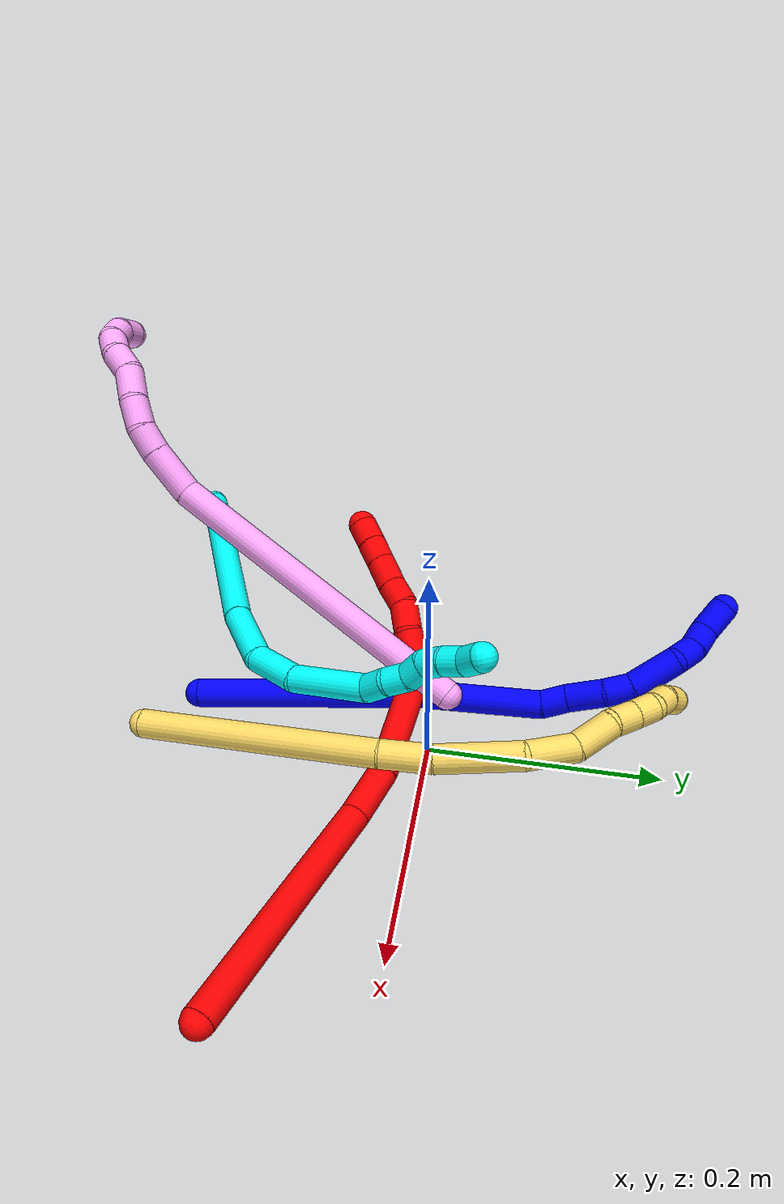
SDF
<sdf version="1.7">
 <world name="default">
  <plugin name="TubeGeneratorPlugin" filename="libtube_generator_plugin.so"/>
  <model name="photoneo_s_sensor">
   <static>1</static>
   <pose>0 0 2 1.57079 1.57079 3.14159</pose>
   <link name="link">
    <inertial><mass>0.1</mass></inertial>
    <sensor name="sensor" type="depth">
     <update_rate>30</update_rate>
     <camera>
      <horizontal_fov>1.22</horizontal_fov>
      <image><width>1920</width><height>1200</height><format>B8G8R8</format></image>
      <clip><near>0.1</near><far>4</far></clip>
      <depth_camera><output>points</output></depth_camera>
     </camera>
     <plugin name="camera_plugin" filename="libgazebo_ros_depth_camera.so">
      <baseline>0.2</baseline>
      <alwaysOn>1</alwaysOn>
      <updateRate>0.0</updateRate>
      <cameraName>camera_ir</cameraName>
      <imageTopicName>/camera/color/image_raw</imageTopicName>
      <cameraInfoTopicName>/camera/color/camera_info</cameraInfoTopicName>
      <depthImageTopicName>/camera/depth/image_raw</depthImageTopicName>
      <depthImageCameraInfoTopicName>/camera/depth/camera_info</depthImageCameraInfoTopicName>
      <pointCloudTopicName>/camera/depth/points</pointCloudTopicName>
      <frameName>fr_optical</frameName>
      <pointCloudCutoff>0.1</pointCloudCutoff>
      <pointCloudCutoffMax>2.0</pointCloudCutoffMax>
      <distortionK1>0</distortionK1>
      <distortionK2>0</distortionK2>
      <distortionK3>0</distortionK3>
      <distortionT1>0</distortionT1>
      <distortionT2>0</distortionT2>
      <CxPrime>0</CxPrime>
      <Cx>0</Cx>
      <Cy>0</Cy>
      <focalLength>0</focalLength>
      <hackBaseline>0</hackBaseline>
     </plugin>
    </sensor>
   </link>
  </model>
  <gravity>0 0 -9.8</gravity>
  <magnetic_field>6e-06 2.3e-05 -4.2e-05</magnetic_field>
  <atmosphere type="adiabatic"/>
  <physics name="default_physics" default="0" type="ode">
   <max_step_size>0.003</max_step_size>
   <real_time_factor>1</real_time_factor>
   <real_time_update_rate>1000</real_time_update_rate>
   <max_contacts>10000</max_contacts>
   <ode>
    <solver>
     <type>quick</type>
     <iters>100</iters>
     <sor>1.3</sor>
     <use_dynamic_moi_rescaling>0</use_dynamic_moi_rescaling>
    </solver>
    <constraints>
     <contact_max_correcting_vel>0</contact_max_correcting_vel>
     <contact_surface_layer>0.001</contact_surface_layer>
     <cfm>0</cfm>
     <erp>0.2</erp>
    </constraints>
   </ode>
  </physics>
  <scene><ambient>0.4 0.4 0.4 1</ambient><background>0.7 0.7 0.7 1</background><shadows>0</shadows></scene>
  <audio><device>default</device></audio>
  <spherical_coordinates>
   <surface_model>EARTH_WGS84</surface_model>
   <latitude_deg>0</latitude_deg>
   <longitude_deg>0</longitude_deg>
   <elevation>0</elevation>
   <heading_deg>0</heading_deg>
  </spherical_coordinates>
  <model name="bin">
   <static>1</static>
   <link name="bottom">
    <collision name="collision-bottom">
     <pose>0 0 -0.01 0 -0 0</pose>
     <geometry><box><size>0.8 0.6 0.02</size></box></geometry>
     <surface>
      <friction><ode><mu>100</mu><mu2>100</mu2></ode></friction>
      <contact><collide_bitmask>65535</collide_bitmask></contact>
     </surface>
    </collision>
   </link>
   <link name="west_wall">
    <collision name="collision-west_wall">
     <pose>-0.41 0 0.1 0 -0 0</pose>
     <geometry><box><size>0.02 0.6 0.2</size></box></geometry>
     <surface>
      <friction><ode><mu>100</mu><mu2>100</mu2></ode></friction>
      <contact><collide_bitmask>65535</collide_bitmask></contact>
     </surface>
    </collision>
   </link>
   <link name="east_wall">
    <collision name="collision-east_wall">
     <pose>0.41 0 0.1 0 -0 0</pose>
     <geometry><box><size>0.02 0.6 0.2</size></box></geometry>
     <surface>
      <friction><ode><mu>100</mu><mu2>100</mu2></ode></friction>
      <contact><collide_bitmask>65535</collide_bitmask></contact>
     </surface>
    </collision>
   </link>
   <link name="south_wall">
    <collision name="collision-south_wall">
     <pose>0 -0.31 0.1 0 -0 0</pose>
     <geometry><box><size>0.8 0.02 0.2</size></box></geometry>
     <surface>
      <friction><ode><mu>100</mu><mu2>100</mu2></ode></friction>
      <contact><collide_bitmask>65535</collide_bitmask></contact>
     </surface>
    </collision>
   </link>
   <link name="north_wall">
    <collision name="collision-north_wall">
     <pose>0 0.31 0.1 0 -0 0</pose>
     <geometry><box><size>0.8 0.02 0.2</size></box></geometry>
     <surface>
      <friction><ode><mu>100</mu><mu2>100</mu2></ode></friction>
      <contact><collide_bitmask>65535</collide_bitmask></contact>
     </surface>
    </collision>
   </link>
  </model>
  <model name="1">
   <static>0</static>
   <link name="1">
    <collision name="collision-cylinder-e_1_1_4">
     <pose>-0.009485 0.097593 -0.002834 -1.59983 -0.09684 0.099688</pose>
     <geometry><cylinder><radius>0.0125</radius><length>0.196188</length></cylinder></geometry>
     <surface>
      <friction><ode><mu>1.16</mu><mu2>1.16</mu2><slip1>0</slip1><slip2>0</slip2></ode></friction>
      <contact><ode><kp>1e+06</kp><kd>1</kd><max_vel>0</max_vel><min_depth>0.001</min_depth></ode></contact>
     </surface>
    </collision>
    <visual name="visual-cylinder-e_1_1_4">
     <pose>-0.009485 0.097593 -0.002834 -1.59983 -0.09684 0.099688</pose>
     <geometry><cylinder><radius>0.0125</radius><length>0.196188</length></cylinder></geometry>
     <material><ambient>0 0 1 1</ambient></material>
    </visual>
    <collision name="collision-cylinder-e_2_4_5">
     <pose>-0.019426 0.248966 -0.009123 -1.63495 -0.00847 0.009031</pose>
     <geometry><cylinder><radius>0.0125</radius><length>0.107785</length></cylinder></geometry>
     <surface>
      <friction><ode><mu>1.16</mu><mu2>1.16</mu2><slip1>0</slip1><slip2>0</slip2></ode></friction>
      <contact><ode><kp>1e+06</kp><kd>1</kd><max_vel>0</max_vel><min_depth>0.001</min_depth></ode></contact>
     </surface>
    </collision>
    <visual name="visual-cylinder-e_2_4_5">
     <pose>-0.019426 0.248966 -0.009123 -1.63495 -0.00847 0.009031</pose>
     <geometry><cylinder><radius>0.0125</radius><length>0.107785</length></cylinder></geometry>
     <material><ambient>0 0 1 1</ambient></material>
    </visual>
    <collision name="collision-cylinder-e_3_5_6">
     <pose>-0.024044 0.313955 -0.011457 -1.47107 -0.353862 0.320826</pose>
     <geometry><cylinder><radius>0.0125</radius><length>0.024019</length></cylinder></geometry>
     <surface>
      <friction><ode><mu>1.16</mu><mu2>1.16</mu2><slip1>0</slip1><slip2>0</slip2></ode></friction>
      <contact><ode><kp>1e+06</kp><kd>1</kd><max_vel>0</max_vel><min_depth>0.001</min_depth></ode></contact>
     </surface>
    </collision>
    <visual name="visual-cylinder-e_3_5_6">
     <pose>-0.024044 0.313955 -0.011457 -1.47107 -0.353862 0.320826</pose>
     <geometry><cylinder><radius>0.0125</radius><length>0.024019</length></cylinder></geometry>
     <material><ambient>0 0 1 1</ambient></material>
    </visual>
    <collision name="collision-cylinder-e_4_6_7">
     <pose>-0.032453 0.340604 -0.006381 -1.32008 -0.260485 0.202635</pose>
     <geometry><cylinder><radius>0.0125</radius><length>0.032988</length></cylinder></geometry>
     <surface>
      <friction><ode><mu>1.16</mu><mu2>1.16</mu2><slip1>0</slip1><slip2>0</slip2></ode></friction>
      <contact><ode><kp>1e+06</kp><kd>1</kd><max_vel>0</max_vel><min_depth>0.001</min_depth></ode></contact>
     </surface>
    </collision>
    <visual name="visual-cylinder-e_4_6_7">
     <pose>-0.032453 0.340604 -0.006381 -1.32008 -0.260485 0.202635</pose>
     <geometry><cylinder><radius>0.0125</radius><length>0.032988</length></cylinder></geometry>
     <material><ambient>0 0 1 1</ambient></material>
    </visual>
    <collision name="collision-cylinder-e_5_7_8">
     <pose>-0.040402 0.36718 -0.002001 -1.53257 -0.320599 0.308767</pose>
     <geometry><cylinder><radius>0.0125</radius><length>0.023488</length></cylinder></geometry>
     <surface>
      <friction><ode><mu>1.16</mu><mu2>1.16</mu2><slip1>0</slip1><slip2>0</slip2></ode></friction>
      <contact><ode><kp>1e+06</kp><kd>1</kd><max_vel>0</max_vel><min_depth>0.001</min_depth></ode></contact>
     </surface>
    </collision>
    <visual name="visual-cylinder-e_5_7_8">
     <pose>-0.040402 0.36718 -0.002001 -1.53257 -0.320599 0.308767</pose>
     <geometry><cylinder><radius>0.0125</radius><length>0.023488</length></cylinder></geometry>
     <material><ambient>0 0 1 1</ambient></material>
    </visual>
    <collision name="collision-cylinder-e_6_8_9">
     <pose>-0.057604 0.39625 -0.002236 -1.60762 -0.645007 0.667476</pose>
     <geometry><cylinder><radius>0.0125</radius><length>0.044913</length></cylinder></geometry>
     <surface>
      <friction><ode><mu>1.16</mu><mu2>1.16</mu2><slip1>0</slip1><slip2>0</slip2></ode></friction>
      <contact><ode><kp>1e+06</kp><kd>1</kd><max_vel>0</max_vel><min_depth>0.001</min_depth></ode></contact>
     </surface>
    </collision>
    <visual name="visual-cylinder-e_6_8_9">
     <pose>-0.057604 0.39625 -0.002236 -1.60762 -0.645007 0.667476</pose>
     <geometry><cylinder><radius>0.0125</radius><length>0.044913</length></cylinder></geometry>
     <material><ambient>0 0 1 1</ambient></material>
    </visual>
    <collision name="collision-cylinder-e_7_9_10">
     <pose>-0.07673 0.421889 -0.008161 -2.17018 -0.542462 0.969691</pose>
     <geometry><cylinder><radius>0.0125</radius><length>0.021794</length></cylinder></geometry>
     <surface>
      <friction><ode><mu>1.16</mu><mu2>1.16</mu2><slip1>0</slip1><slip2>0</slip2></ode></friction>
      <contact><ode><kp>1e+06</kp><kd>1</kd><max_vel>0</max_vel><min_depth>0.001</min_depth></ode></contact>
     </surface>
    </collision>
    <visual name="visual-cylinder-e_7_9_10">
     <pose>-0.07673 0.421889 -0.008161 -2.17018 -0.542462 0.969691</pose>
     <geometry><cylinder><radius>0.0125</radius><length>0.021794</length></cylinder></geometry>
     <material><ambient>0 0 1 1</ambient></material>
    </visual>
    <collision name="collision-cylinder-e_8_10_11">
     <pose>-0.0904 0.434353 -0.017836 -2.31825 -0.892091 1.66161</pose>
     <geometry><cylinder><radius>0.0125</radius><length>0.02067</length></cylinder></geometry>
     <surface>
      <friction><ode><mu>1.16</mu><mu2>1.16</mu2><slip1>0</slip1><slip2>0</slip2></ode></friction>
      <contact><ode><kp>1e+06</kp><kd>1</kd><max_vel>0</max_vel><min_depth>0.001</min_depth></ode></contact>
     </surface>
    </collision>
    <visual name="visual-cylinder-e_8_10_11">
     <pose>-0.0904 0.434353 -0.017836 -2.31825 -0.892091 1.66161</pose>
     <geometry><cylinder><radius>0.0125</radius><length>0.02067</length></cylinder></geometry>
     <material><ambient>0 0 1 1</ambient></material>
    </visual>
    <collision name="collision-cylinder-e_9_11_2">
     <pose>-0.109429 0.447163 -0.025812 -1.98773 -0.895082 1.27104</pose>
     <geometry><cylinder><radius>0.0125</radius><length>0.028156</length></cylinder></geometry>
     <surface>
      <friction><ode><mu>1.16</mu><mu2>1.16</mu2><slip1>0</slip1><slip2>0</slip2></ode></friction>
      <contact><ode><kp>1e+06</kp><kd>1</kd><max_vel>0</max_vel><min_depth>0.001</min_depth></ode></contact>
     </surface>
    </collision>
    <visual name="visual-cylinder-e_9_11_2">
     <pose>-0.109429 0.447163 -0.025812 -1.98773 -0.895082 1.27104</pose>
     <geometry><cylinder><radius>0.0125</radius><length>0.028156</length></cylinder></geometry>
     <material><ambient>0 0 1 1</ambient></material>
    </visual>
    <collision name="collision-sphere-2">
     <pose>-0.120414 0.455213 -0.029378 0 -0 0</pose>
     <geometry><sphere><radius>0.0125</radius></sphere></geometry>
     <surface>
      <friction><ode><mu>1.16</mu><mu2>1.16</mu2><slip1>0</slip1><slip2>0</slip2></ode></friction>
      <contact><ode><kp>1e+06</kp><kd>1</kd><max_vel>0</max_vel><min_depth>0.001</min_depth></ode></contact>
     </surface>
    </collision>
    <visual name="visual-sphere-2">
     <pose>-0.120414 0.455213 -0.029378 0 -0 0</pose>
     <geometry><sphere><radius>0.0125</radius></sphere></geometry>
     <material><ambient>0 0 1 1</ambient></material>
    </visual>
    <collision name="collision-sphere-11">
     <pose>-0.098445 0.439112 -0.022247 0 -0 0</pose>
     <geometry><sphere><radius>0.0125</radius></sphere></geometry>
     <surface>
      <friction><ode><mu>1.16</mu><mu2>1.16</mu2><slip1>0</slip1><slip2>0</slip2></ode></friction>
      <contact><ode><kp>1e+06</kp><kd>1</kd><max_vel>0</max_vel><min_depth>0.001</min_depth></ode></contact>
     </surface>
    </collision>
    <visual name="visual-sphere-11">
     <pose>-0.098445 0.439112 -0.022247 0 -0 0</pose>
     <geometry><sphere><radius>0.0125</radius></sphere></geometry>
     <material><ambient>0 0 1 1</ambient></material>
    </visual>
    <collision name="collision-sphere-10">
     <pose>-0.082356 0.429595 -0.013426 0 -0 0</pose>
     <geometry><sphere><radius>0.0125</radius></sphere></geometry>
     <surface>
      <friction><ode><mu>1.16</mu><mu2>1.16</mu2><slip1>0</slip1><slip2>0</slip2></ode></friction>
      <contact><ode><kp>1e+06</kp><kd>1</kd><max_vel>0</max_vel><min_depth>0.001</min_depth></ode></contact>
     </surface>
    </collision>
    <visual name="visual-sphere-10">
     <pose>-0.082356 0.429595 -0.013426 0 -0 0</pose>
     <geometry><sphere><radius>0.0125</radius></sphere></geometry>
     <material><ambient>0 0 1 1</ambient></material>
    </visual>
    <collision name="collision-sphere-9">
     <pose>-0.071105 0.414183 -0.002896 0 -0 0</pose>
     <geometry><sphere><radius>0.0125</radius></sphere></geometry>
     <surface>
      <friction><ode><mu>1.16</mu><mu2>1.16</mu2><slip1>0</slip1><slip2>0</slip2></ode></friction>
      <contact><ode><kp>1e+06</kp><kd>1</kd><max_vel>0</max_vel><min_depth>0.001</min_depth></ode></contact>
     </surface>
    </collision>
    <visual name="visual-sphere-9">
     <pose>-0.071105 0.414183 -0.002896 0 -0 0</pose>
     <geometry><sphere><radius>0.0125</radius></sphere></geometry>
     <material><ambient>0 0 1 1</ambient></material>
    </visual>
    <collision name="collision-sphere-4">
     <pose>-0.018969 0.195186 -0.005669 0 -0 0</pose>
     <geometry><sphere><radius>0.0125</radius></sphere></geometry>
     <surface>
      <friction><ode><mu>1.16</mu><mu2>1.16</mu2><slip1>0</slip1><slip2>0</slip2></ode></friction>
      <contact><ode><kp>1e+06</kp><kd>1</kd><max_vel>0</max_vel><min_depth>0.001</min_depth></ode></contact>
     </surface>
    </collision>
    <visual name="visual-sphere-4">
     <pose>-0.018969 0.195186 -0.005669 0 -0 0</pose>
     <geometry><sphere><radius>0.0125</radius></sphere></geometry>
     <material><ambient>0 0 1 1</ambient></material>
    </visual>
    <collision name="collision-sphere-1">
     <geometry><sphere><radius>0.0125</radius></sphere></geometry>
     <surface>
      <friction><ode><mu>1.16</mu><mu2>1.16</mu2><slip1>0</slip1><slip2>0</slip2></ode></friction>
      <contact><ode><kp>1e+06</kp><kd>1</kd><max_vel>0</max_vel><min_depth>0.001</min_depth></ode></contact>
     </surface>
    </collision>
    <visual name="visual-sphere-1">
     <geometry><sphere><radius>0.0125</radius></sphere></geometry>
     <material><ambient>0 0 1 1</ambient></material>
    </visual>
    <collision name="collision-sphere-8">
     <pose>-0.044103 0.378318 -0.001575 0 -0 0</pose>
     <geometry><sphere><radius>0.0125</radius></sphere></geometry>
     <surface>
      <friction><ode><mu>1.16</mu><mu2>1.16</mu2><slip1>0</slip1><slip2>0</slip2></ode></friction>
      <contact><ode><kp>1e+06</kp><kd>1</kd><max_vel>0</max_vel><min_depth>0.001</min_depth></ode></contact>
     </surface>
    </collision>
    <visual name="visual-sphere-8">
     <pose>-0.044103 0.378318 -0.001575 0 -0 0</pose>
     <geometry><sphere><radius>0.0125</radius></sphere></geometry>
     <material><ambient>0 0 1 1</ambient></material>
    </visual>
    <collision name="collision-sphere-5">
     <pose>-0.019882 0.302746 -0.012578 0 -0 0</pose>
     <geometry><sphere><radius>0.0125</radius></sphere></geometry>
     <surface>
      <friction><ode><mu>1.16</mu><mu2>1.16</mu2><slip1>0</slip1><slip2>0</slip2></ode></friction>
      <contact><ode><kp>1e+06</kp><kd>1</kd><max_vel>0</max_vel><min_depth>0.001</min_depth></ode></contact>
     </surface>
    </collision>
    <visual name="visual-sphere-5">
     <pose>-0.019882 0.302746 -0.012578 0 -0 0</pose>
     <geometry><sphere><radius>0.0125</radius></sphere></geometry>
     <material><ambient>0 0 1 1</ambient></material>
    </visual>
    <collision name="collision-sphere-6">
     <pose>-0.028205 0.325165 -0.010335 0 -0 0</pose>
     <geometry><sphere><radius>0.0125</radius></sphere></geometry>
     <surface>
      <friction><ode><mu>1.16</mu><mu2>1.16</mu2><slip1>0</slip1><slip2>0</slip2></ode></friction>
      <contact><ode><kp>1e+06</kp><kd>1</kd><max_vel>0</max_vel><min_depth>0.001</min_depth></ode></contact>
     </surface>
    </collision>
    <visual name="visual-sphere-6">
     <pose>-0.028205 0.325165 -0.010335 0 -0 0</pose>
     <geometry><sphere><radius>0.0125</radius></sphere></geometry>
     <material><ambient>0 0 1 1</ambient></material>
    </visual>
    <collision name="collision-sphere-7">
     <pose>-0.036701 0.356043 -0.002427 0 -0 0</pose>
     <geometry><sphere><radius>0.0125</radius></sphere></geometry>
     <surface>
      <friction><ode><mu>1.16</mu><mu2>1.16</mu2><slip1>0</slip1><slip2>0</slip2></ode></friction>
      <contact><ode><kp>1e+06</kp><kd>1</kd><max_vel>0</max_vel><min_depth>0.001</min_depth></ode></contact>
     </surface>
    </collision>
    <visual name="visual-sphere-7">
     <pose>-0.036701 0.356043 -0.002427 0 -0 0</pose>
     <geometry><sphere><radius>0.0125</radius></sphere></geometry>
     <material><ambient>0 0 1 1</ambient></material>
    </visual>
    <inertial>
     <pose>-0.031521 0.243884 -0.006892 0 -0 0</pose>
     <mass>0.5</mass>
     <inertia>
      <ixx>0.000819</ixx>
      <ixy>0</ixy>
      <ixz>0</ixz>
      <iyy>9.9e-05</iyy>
      <iyz>0</iyz>
      <izz>-0.000688</izz>
     </inertia>
    </inertial>
   </link>
   <pose>-0.020599 -0.208778 0.011798 -0.02393 0.789177 0.024272</pose>
  </model>
  <model name="2">
   <static>0</static>
   <link name="2">
    <collision name="collision-cylinder-e_1_1_4">
     <pose>-0.019762 0.007416 -0.10188 -3.06893 -0.191101 2.41665</pose>
     <geometry><cylinder><radius>0.0125</radius><length>0.208087</length></cylinder></geometry>
     <surface>
      <friction><ode><mu>1.16</mu><mu2>1.16</mu2><slip1>0</slip1><slip2>0</slip2></ode></friction>
      <contact><ode><kp>1e+06</kp><kd>1</kd><max_vel>0</max_vel><min_depth>0.001</min_depth></ode></contact>
     </surface>
    </collision>
    <visual name="visual-cylinder-e_1_1_4">
     <pose>-0.019762 0.007416 -0.10188 -3.06893 -0.191101 2.41665</pose>
     <geometry><cylinder><radius>0.0125</radius><length>0.208087</length></cylinder></geometry>
     <material><ambient>1 0 0 1</ambient></material>
    </visual>
    <collision name="collision-cylinder-e_2_4_5">
     <pose>-0.046739 0.02101 -0.224836 -2.85642 -0.31741 1.67933</pose>
     <geometry><cylinder><radius>0.0125</radius><length>0.046238</length></cylinder></geometry>
     <surface>
      <friction><ode><mu>1.16</mu><mu2>1.16</mu2><slip1>0</slip1><slip2>0</slip2></ode></friction>
      <contact><ode><kp>1e+06</kp><kd>1</kd><max_vel>0</max_vel><min_depth>0.001</min_depth></ode></contact>
     </surface>
    </collision>
    <visual name="visual-cylinder-e_2_4_5">
     <pose>-0.046739 0.02101 -0.224836 -2.85642 -0.31741 1.67933</pose>
     <geometry><cylinder><radius>0.0125</radius><length>0.046238</length></cylinder></geometry>
     <material><ambient>1 0 0 1</ambient></material>
    </visual>
    <collision name="collision-cylinder-e_3_5_6">
     <pose>-0.07687 0.040374 -0.276917 -2.73949 -0.597277 1.97202</pose>
     <geometry><cylinder><radius>0.0125</radius><length>0.08149</length></cylinder></geometry>
     <surface>
      <friction><ode><mu>1.16</mu><mu2>1.16</mu2><slip1>0</slip1><slip2>0</slip2></ode></friction>
      <contact><ode><kp>1e+06</kp><kd>1</kd><max_vel>0</max_vel><min_depth>0.001</min_depth></ode></contact>
     </surface>
    </collision>
    <visual name="visual-cylinder-e_3_5_6">
     <pose>-0.07687 0.040374 -0.276917 -2.73949 -0.597277 1.97202</pose>
     <geometry><cylinder><radius>0.0125</radius><length>0.08149</length></cylinder></geometry>
     <material><ambient>1 0 0 1</ambient></material>
    </visual>
    <collision name="collision-cylinder-e_4_6_7">
     <pose>-0.108039 0.055957 -0.315151 -2.82132 -0.82549 2.43486</pose>
     <geometry><cylinder><radius>0.0125</radius><length>0.022463</length></cylinder></geometry>
     <surface>
      <friction><ode><mu>1.16</mu><mu2>1.16</mu2><slip1>0</slip1><slip2>0</slip2></ode></friction>
      <contact><ode><kp>1e+06</kp><kd>1</kd><max_vel>0</max_vel><min_depth>0.001</min_depth></ode></contact>
     </surface>
    </collision>
    <visual name="visual-cylinder-e_4_6_7">
     <pose>-0.108039 0.055957 -0.315151 -2.82132 -0.82549 2.43486</pose>
     <geometry><cylinder><radius>0.0125</radius><length>0.022463</length></cylinder></geometry>
     <material><ambient>1 0 0 1</ambient></material>
    </visual>
    <collision name="collision-cylinder-e_5_7_8">
     <pose>-0.129131 0.060956 -0.326769 -2.60659 -1.19264 2.37406</pose>
     <geometry><cylinder><radius>0.0125</radius><length>0.027629</length></cylinder></geometry>
     <surface>
      <friction><ode><mu>1.16</mu><mu2>1.16</mu2><slip1>0</slip1><slip2>0</slip2></ode></friction>
      <contact><ode><kp>1e+06</kp><kd>1</kd><max_vel>0</max_vel><min_depth>0.001</min_depth></ode></contact>
     </surface>
    </collision>
    <visual name="visual-cylinder-e_5_7_8">
     <pose>-0.129131 0.060956 -0.326769 -2.60659 -1.19264 2.37406</pose>
     <geometry><cylinder><radius>0.0125</radius><length>0.027629</length></cylinder></geometry>
     <material><ambient>1 0 0 1</ambient></material>
    </visual>
    <collision name="collision-cylinder-e_6_8_9">
     <pose>-0.152611 0.064238 -0.337738 -3.03842 -1.01448 2.95631</pose>
     <geometry><cylinder><radius>0.0125</radius><length>0.025061</length></cylinder></geometry>
     <surface>
      <friction><ode><mu>1.16</mu><mu2>1.16</mu2><slip1>0</slip1><slip2>0</slip2></ode></friction>
      <contact><ode><kp>1e+06</kp><kd>1</kd><max_vel>0</max_vel><min_depth>0.001</min_depth></ode></contact>
     </surface>
    </collision>
    <visual name="visual-cylinder-e_6_8_9">
     <pose>-0.152611 0.064238 -0.337738 -3.03842 -1.01448 2.95631</pose>
     <geometry><cylinder><radius>0.0125</radius><length>0.025061</length></cylinder></geometry>
     <material><ambient>1 0 0 1</ambient></material>
    </visual>
    <collision name="collision-cylinder-e_7_9_10">
     <pose>-0.173646 0.062414 -0.348091 2.55527 -1.16002 -2.27811</pose>
     <geometry><cylinder><radius>0.0125</radius><length>0.022676</length></cylinder></geometry>
     <surface>
      <friction><ode><mu>1.16</mu><mu2>1.16</mu2><slip1>0</slip1><slip2>0</slip2></ode></friction>
      <contact><ode><kp>1e+06</kp><kd>1</kd><max_vel>0</max_vel><min_depth>0.001</min_depth></ode></contact>
     </surface>
    </collision>
    <visual name="visual-cylinder-e_7_9_10">
     <pose>-0.173646 0.062414 -0.348091 2.55527 -1.16002 -2.27811</pose>
     <geometry><cylinder><radius>0.0125</radius><length>0.022676</length></cylinder></geometry>
     <material><ambient>1 0 0 1</ambient></material>
    </visual>
    <collision name="collision-cylinder-e_8_10_11">
     <pose>-0.196058 0.058615 -0.356077 2.84368 -1.21922 -2.71825</pose>
     <geometry><cylinder><radius>0.0125</radius><length>0.025599</length></cylinder></geometry>
     <surface>
      <friction><ode><mu>1.16</mu><mu2>1.16</mu2><slip1>0</slip1><slip2>0</slip2></ode></friction>
      <contact><ode><kp>1e+06</kp><kd>1</kd><max_vel>0</max_vel><min_depth>0.001</min_depth></ode></contact>
     </surface>
    </collision>
    <visual name="visual-cylinder-e_8_10_11">
     <pose>-0.196058 0.058615 -0.356077 2.84368 -1.21922 -2.71825</pose>
     <geometry><cylinder><radius>0.0125</radius><length>0.025599</length></cylinder></geometry>
     <material><ambient>1 0 0 1</ambient></material>
    </visual>
    <collision name="collision-cylinder-e_9_11_12">
     <pose>-0.217572 0.056258 -0.363409 2.81313 -1.23685 -2.68393</pose>
     <geometry><cylinder><radius>0.0125</radius><length>0.020106</length></cylinder></geometry>
     <surface>
      <friction><ode><mu>1.16</mu><mu2>1.16</mu2><slip1>0</slip1><slip2>0</slip2></ode></friction>
      <contact><ode><kp>1e+06</kp><kd>1</kd><max_vel>0</max_vel><min_depth>0.001</min_depth></ode></contact>
     </surface>
    </collision>
    <visual name="visual-cylinder-e_9_11_12">
     <pose>-0.217572 0.056258 -0.363409 2.81313 -1.23685 -2.68393</pose>
     <geometry><cylinder><radius>0.0125</radius><length>0.020106</length></cylinder></geometry>
     <material><ambient>1 0 0 1</ambient></material>
    </visual>
    <collision name="collision-cylinder-e_10_12_2">
     <pose>-0.236743 0.053934 -0.369911 2.78454 -1.21363 -2.63297</pose>
     <geometry><cylinder><radius>0.0125</radius><length>0.02065</length></cylinder></geometry>
     <surface>
      <friction><ode><mu>1.16</mu><mu2>1.16</mu2><slip1>0</slip1><slip2>0</slip2></ode></friction>
      <contact><ode><kp>1e+06</kp><kd>1</kd><max_vel>0</max_vel><min_depth>0.001</min_depth></ode></contact>
     </surface>
    </collision>
    <visual name="visual-cylinder-e_10_12_2">
     <pose>-0.236743 0.053934 -0.369911 2.78454 -1.21363 -2.63297</pose>
     <geometry><cylinder><radius>0.0125</radius><length>0.02065</length></cylinder></geometry>
     <material><ambient>1 0 0 1</ambient></material>
    </visual>
    <collision name="collision-sphere-2">
     <pose>-0.246417 0.052672 -0.373293 0 -0 0</pose>
     <geometry><sphere><radius>0.0125</radius></sphere></geometry>
     <surface>
      <friction><ode><mu>1.16</mu><mu2>1.16</mu2><slip1>0</slip1><slip2>0</slip2></ode></friction>
      <contact><ode><kp>1e+06</kp><kd>1</kd><max_vel>0</max_vel><min_depth>0.001</min_depth></ode></contact>
     </surface>
    </collision>
    <visual name="visual-sphere-2">
     <pose>-0.246417 0.052672 -0.373293 0 -0 0</pose>
     <geometry><sphere><radius>0.0125</radius></sphere></geometry>
     <material><ambient>1 0 0 1</ambient></material>
    </visual>
    <collision name="collision-sphere-12">
     <pose>-0.22707 0.055195 -0.366528 0 -0 0</pose>
     <geometry><sphere><radius>0.0125</radius></sphere></geometry>
     <surface>
      <friction><ode><mu>1.16</mu><mu2>1.16</mu2><slip1>0</slip1><slip2>0</slip2></ode></friction>
      <contact><ode><kp>1e+06</kp><kd>1</kd><max_vel>0</max_vel><min_depth>0.001</min_depth></ode></contact>
     </surface>
    </collision>
    <visual name="visual-sphere-12">
     <pose>-0.22707 0.055195 -0.366528 0 -0 0</pose>
     <geometry><sphere><radius>0.0125</radius></sphere></geometry>
     <material><ambient>1 0 0 1</ambient></material>
    </visual>
    <collision name="collision-sphere-11">
     <pose>-0.208074 0.057321 -0.36029 0 -0 0</pose>
     <geometry><sphere><radius>0.0125</radius></sphere></geometry>
     <surface>
      <friction><ode><mu>1.16</mu><mu2>1.16</mu2><slip1>0</slip1><slip2>0</slip2></ode></friction>
      <contact><ode><kp>1e+06</kp><kd>1</kd><max_vel>0</max_vel><min_depth>0.001</min_depth></ode></contact>
     </surface>
    </collision>
    <visual name="visual-sphere-11">
     <pose>-0.208074 0.057321 -0.36029 0 -0 0</pose>
     <geometry><sphere><radius>0.0125</radius></sphere></geometry>
     <material><ambient>1 0 0 1</ambient></material>
    </visual>
    <collision name="collision-sphere-10">
     <pose>-0.184041 0.059909 -0.351863 0 -0 0</pose>
     <geometry><sphere><radius>0.0125</radius></sphere></geometry>
     <surface>
      <friction><ode><mu>1.16</mu><mu2>1.16</mu2><slip1>0</slip1><slip2>0</slip2></ode></friction>
      <contact><ode><kp>1e+06</kp><kd>1</kd><max_vel>0</max_vel><min_depth>0.001</min_depth></ode></contact>
     </surface>
    </collision>
    <visual name="visual-sphere-10">
     <pose>-0.184041 0.059909 -0.351863 0 -0 0</pose>
     <geometry><sphere><radius>0.0125</radius></sphere></geometry>
     <material><ambient>1 0 0 1</ambient></material>
    </visual>
    <collision name="collision-sphere-9">
     <pose>-0.163252 0.064919 -0.34432 0 -0 0</pose>
     <geometry><sphere><radius>0.0125</radius></sphere></geometry>
     <surface>
      <friction><ode><mu>1.16</mu><mu2>1.16</mu2><slip1>0</slip1><slip2>0</slip2></ode></friction>
      <contact><ode><kp>1e+06</kp><kd>1</kd><max_vel>0</max_vel><min_depth>0.001</min_depth></ode></contact>
     </surface>
    </collision>
    <visual name="visual-sphere-9">
     <pose>-0.163252 0.064919 -0.34432 0 -0 0</pose>
     <geometry><sphere><radius>0.0125</radius></sphere></geometry>
     <material><ambient>1 0 0 1</ambient></material>
    </visual>
    <collision name="collision-sphere-4">
     <pose>-0.039524 0.014831 -0.203759 0 -0 0</pose>
     <geometry><sphere><radius>0.0125</radius></sphere></geometry>
     <surface>
      <friction><ode><mu>1.16</mu><mu2>1.16</mu2><slip1>0</slip1><slip2>0</slip2></ode></friction>
      <contact><ode><kp>1e+06</kp><kd>1</kd><max_vel>0</max_vel><min_depth>0.001</min_depth></ode></contact>
     </surface>
    </collision>
    <visual name="visual-sphere-4">
     <pose>-0.039524 0.014831 -0.203759 0 -0 0</pose>
     <geometry><sphere><radius>0.0125</radius></sphere></geometry>
     <material><ambient>1 0 0 1</ambient></material>
    </visual>
    <collision name="collision-sphere-1">
     <geometry><sphere><radius>0.0125</radius></sphere></geometry>
     <surface>
      <friction><ode><mu>1.16</mu><mu2>1.16</mu2><slip1>0</slip1><slip2>0</slip2></ode></friction>
      <contact><ode><kp>1e+06</kp><kd>1</kd><max_vel>0</max_vel><min_depth>0.001</min_depth></ode></contact>
     </surface>
    </collision>
    <visual name="visual-sphere-1">
     <geometry><sphere><radius>0.0125</radius></sphere></geometry>
     <material><ambient>1 0 0 1</ambient></material>
    </visual>
    <collision name="collision-sphere-8">
     <pose>-0.14197 0.063556 -0.331157 0 -0 0</pose>
     <geometry><sphere><radius>0.0125</radius></sphere></geometry>
     <surface>
      <friction><ode><mu>1.16</mu><mu2>1.16</mu2><slip1>0</slip1><slip2>0</slip2></ode></friction>
      <contact><ode><kp>1e+06</kp><kd>1</kd><max_vel>0</max_vel><min_depth>0.001</min_depth></ode></contact>
     </surface>
    </collision>
    <visual name="visual-sphere-8">
     <pose>-0.14197 0.063556 -0.331157 0 -0 0</pose>
     <geometry><sphere><radius>0.0125</radius></sphere></geometry>
     <material><ambient>1 0 0 1</ambient></material>
    </visual>
    <collision name="collision-sphere-5">
     <pose>-0.053955 0.027189 -0.245913 0 -0 0</pose>
     <geometry><sphere><radius>0.0125</radius></sphere></geometry>
     <surface>
      <friction><ode><mu>1.16</mu><mu2>1.16</mu2><slip1>0</slip1><slip2>0</slip2></ode></friction>
      <contact><ode><kp>1e+06</kp><kd>1</kd><max_vel>0</max_vel><min_depth>0.001</min_depth></ode></contact>
     </surface>
    </collision>
    <visual name="visual-sphere-5">
     <pose>-0.053955 0.027189 -0.245913 0 -0 0</pose>
     <geometry><sphere><radius>0.0125</radius></sphere></geometry>
     <material><ambient>1 0 0 1</ambient></material>
    </visual>
    <collision name="collision-sphere-6">
     <pose>-0.099785 0.053559 -0.307921 0 -0 0</pose>
     <geometry><sphere><radius>0.0125</radius></sphere></geometry>
     <surface>
      <friction><ode><mu>1.16</mu><mu2>1.16</mu2><slip1>0</slip1><slip2>0</slip2></ode></friction>
      <contact><ode><kp>1e+06</kp><kd>1</kd><max_vel>0</max_vel><min_depth>0.001</min_depth></ode></contact>
     </surface>
    </collision>
    <visual name="visual-sphere-6">
     <pose>-0.099785 0.053559 -0.307921 0 -0 0</pose>
     <geometry><sphere><radius>0.0125</radius></sphere></geometry>
     <material><ambient>1 0 0 1</ambient></material>
    </visual>
    <collision name="collision-sphere-7">
     <pose>-0.116293 0.058355 -0.322381 0 -0 0</pose>
     <geometry><sphere><radius>0.0125</radius></sphere></geometry>
     <surface>
      <friction><ode><mu>1.16</mu><mu2>1.16</mu2><slip1>0</slip1><slip2>0</slip2></ode></friction>
      <contact><ode><kp>1e+06</kp><kd>1</kd><max_vel>0</max_vel><min_depth>0.001</min_depth></ode></contact>
     </surface>
    </collision>
    <visual name="visual-sphere-7">
     <pose>-0.116293 0.058355 -0.322381 0 -0 0</pose>
     <geometry><sphere><radius>0.0125</radius></sphere></geometry>
     <material><ambient>1 0 0 1</ambient></material>
    </visual>
    <inertial>
     <pose>-0.081153 0.031033 -0.221376 0 -0 0</pose>
     <mass>0.5</mass>
     <inertia>
      <ixx>-5.8e-05</ixx>
      <ixy>0</ixy>
      <ixz>0</ixz>
      <iyy>0.001161</iyy>
      <iyz>0</iyz>
      <izz>8.6e-05</izz>
     </inertia>
    </inertial>
   </link>
   <pose>0.280195 -0.107383 0.049563 1.12414 0.629229 0.886995</pose>
  </model>
  <model name="3">
   <static>0</static>
   <link name="3">
    <collision name="collision-cylinder-e_1_1_4">
     <pose>0.067724 0.040359 -0.060933 -2.55659 0.747336 -1.8317</pose>
     <geometry><cylinder><radius>0.0125</radius><length>0.199281</length></cylinder></geometry>
     <surface>
      <friction><ode><mu>1.16</mu><mu2>1.16</mu2><slip1>0</slip1><slip2>0</slip2></ode></friction>
      <contact><ode><kp>1e+06</kp><kd>1</kd><max_vel>0</max_vel><min_depth>0.001</min_depth></ode></contact>
     </surface>
    </collision>
    <visual name="visual-cylinder-e_1_1_4">
     <pose>0.067724 0.040359 -0.060933 -2.55659 0.747336 -1.8317</pose>
     <geometry><cylinder><radius>0.0125</radius><length>0.199281</length></cylinder></geometry>
     <material><ambient>0.003922 1 0.996078 1</ambient></material>
    </visual>
    <collision name="collision-cylinder-e_2_4_5">
     <pose>0.152649 0.096869 -0.141086 -2.44273 0.600674 -1.40893</pose>
     <geometry><cylinder><radius>0.0125</radius><length>0.060866</length></cylinder></geometry>
     <surface>
      <friction><ode><mu>1.16</mu><mu2>1.16</mu2><slip1>0</slip1><slip2>0</slip2></ode></friction>
      <contact><ode><kp>1e+06</kp><kd>1</kd><max_vel>0</max_vel><min_depth>0.001</min_depth></ode></contact>
     </surface>
    </collision>
    <visual name="visual-cylinder-e_2_4_5">
     <pose>0.152649 0.096869 -0.141086 -2.44273 0.600674 -1.40893</pose>
     <geometry><cylinder><radius>0.0125</radius><length>0.060866</length></cylinder></geometry>
     <material><ambient>0.003922 1 0.996078 1</ambient></material>
    </visual>
    <collision name="collision-cylinder-e_3_5_6">
     <pose>0.175675 0.132021 -0.171334 -2.09668 0.259212 -0.445192</pose>
     <geometry><cylinder><radius>0.0125</radius><length>0.045456</length></cylinder></geometry>
     <surface>
      <friction><ode><mu>1.16</mu><mu2>1.16</mu2><slip1>0</slip1><slip2>0</slip2></ode></friction>
      <contact><ode><kp>1e+06</kp><kd>1</kd><max_vel>0</max_vel><min_depth>0.001</min_depth></ode></contact>
     </surface>
    </collision>
    <visual name="visual-cylinder-e_3_5_6">
     <pose>0.175675 0.132021 -0.171334 -2.09668 0.259212 -0.445192</pose>
     <geometry><cylinder><radius>0.0125</radius><length>0.045456</length></cylinder></geometry>
     <material><ambient>0.003922 1 0.996078 1</ambient></material>
    </visual>
    <collision name="collision-cylinder-e_4_6_7">
     <pose>0.183419 0.1853 -0.191167 -1.82223 0.054135 -0.069787</pose>
     <geometry><cylinder><radius>0.0125</radius><length>0.070888</length></cylinder></geometry>
     <surface>
      <friction><ode><mu>1.16</mu><mu2>1.16</mu2><slip1>0</slip1><slip2>0</slip2></ode></friction>
      <contact><ode><kp>1e+06</kp><kd>1</kd><max_vel>0</max_vel><min_depth>0.001</min_depth></ode></contact>
     </surface>
    </collision>
    <visual name="visual-cylinder-e_4_6_7">
     <pose>0.183419 0.1853 -0.191167 -1.82223 0.054135 -0.069787</pose>
     <geometry><cylinder><radius>0.0125</radius><length>0.070888</length></cylinder></geometry>
     <material><ambient>0.003922 1 0.996078 1</ambient></material>
    </visual>
    <collision name="collision-cylinder-e_5_7_8">
     <pose>0.188736 0.230496 -0.198038 -1.39541 0.29753 -0.249988</pose>
     <geometry><cylinder><radius>0.0125</radius><length>0.023192</length></cylinder></geometry>
     <surface>
      <friction><ode><mu>1.16</mu><mu2>1.16</mu2><slip1>0</slip1><slip2>0</slip2></ode></friction>
      <contact><ode><kp>1e+06</kp><kd>1</kd><max_vel>0</max_vel><min_depth>0.001</min_depth></ode></contact>
     </surface>
    </collision>
    <visual name="visual-cylinder-e_5_7_8">
     <pose>0.188736 0.230496 -0.198038 -1.39541 0.29753 -0.249988</pose>
     <geometry><cylinder><radius>0.0125</radius><length>0.023192</length></cylinder></geometry>
     <material><ambient>0.003922 1 0.996078 1</ambient></material>
    </visual>
    <collision name="collision-cylinder-e_6_8_9">
     <pose>0.192374 0.251469 -0.195311 -1.49218 0.023639 -0.02185</pose>
     <geometry><cylinder><radius>0.0125</radius><length>0.020182</length></cylinder></geometry>
     <surface>
      <friction><ode><mu>1.16</mu><mu2>1.16</mu2><slip1>0</slip1><slip2>0</slip2></ode></friction>
      <contact><ode><kp>1e+06</kp><kd>1</kd><max_vel>0</max_vel><min_depth>0.001</min_depth></ode></contact>
     </surface>
    </collision>
    <visual name="visual-cylinder-e_6_8_9">
     <pose>0.192374 0.251469 -0.195311 -1.49218 0.023639 -0.02185</pose>
     <geometry><cylinder><radius>0.0125</radius><length>0.020182</length></cylinder></geometry>
     <material><ambient>0.003922 1 0.996078 1</ambient></material>
    </visual>
    <collision name="collision-cylinder-e_7_9_10">
     <pose>0.194751 0.270225 -0.190072 -1.09827 0.215488 -0.13218</pose>
     <geometry><cylinder><radius>0.0125</radius><length>0.020004</length></cylinder></geometry>
     <surface>
      <friction><ode><mu>1.16</mu><mu2>1.16</mu2><slip1>0</slip1><slip2>0</slip2></ode></friction>
      <contact><ode><kp>1e+06</kp><kd>1</kd><max_vel>0</max_vel><min_depth>0.001</min_depth></ode></contact>
     </surface>
    </collision>
    <visual name="visual-cylinder-e_7_9_10">
     <pose>0.194751 0.270225 -0.190072 -1.09827 0.215488 -0.13218</pose>
     <geometry><cylinder><radius>0.0125</radius><length>0.020004</length></cylinder></geometry>
     <material><ambient>0.003922 1 0.996078 1</ambient></material>
    </visual>
    <collision name="collision-cylinder-e_8_10_11">
     <pose>0.199993 0.288441 -0.185393 -1.54641 0.315173 -0.307699</pose>
     <geometry><cylinder><radius>0.0125</radius><length>0.020024</length></cylinder></geometry>
     <surface>
      <friction><ode><mu>1.16</mu><mu2>1.16</mu2><slip1>0</slip1><slip2>0</slip2></ode></friction>
      <contact><ode><kp>1e+06</kp><kd>1</kd><max_vel>0</max_vel><min_depth>0.001</min_depth></ode></contact>
     </surface>
    </collision>
    <visual name="visual-cylinder-e_8_10_11">
     <pose>0.199993 0.288441 -0.185393 -1.54641 0.315173 -0.307699</pose>
     <geometry><cylinder><radius>0.0125</radius><length>0.020024</length></cylinder></geometry>
     <material><ambient>0.003922 1 0.996078 1</ambient></material>
    </visual>
    <collision name="collision-cylinder-e_9_11_12">
     <pose>0.205024 0.307717 -0.186392 -1.69631 0.19351 -0.219266</pose>
     <geometry><cylinder><radius>0.0125</radius><length>0.020048</length></cylinder></geometry>
     <surface>
      <friction><ode><mu>1.16</mu><mu2>1.16</mu2><slip1>0</slip1><slip2>0</slip2></ode></friction>
      <contact><ode><kp>1e+06</kp><kd>1</kd><max_vel>0</max_vel><min_depth>0.001</min_depth></ode></contact>
     </surface>
    </collision>
    <visual name="visual-cylinder-e_9_11_12">
     <pose>0.205024 0.307717 -0.186392 -1.69631 0.19351 -0.219266</pose>
     <geometry><cylinder><radius>0.0125</radius><length>0.020048</length></cylinder></geometry>
     <material><ambient>0.003922 1 0.996078 1</ambient></material>
    </visual>
    <collision name="collision-cylinder-e_10_12_2">
     <pose>0.211792 0.326179 -0.186419 -1.43319 0.503583 -0.440881</pose>
     <geometry><cylinder><radius>0.0125</radius><length>0.020061</length></cylinder></geometry>
     <surface>
      <friction><ode><mu>1.16</mu><mu2>1.16</mu2><slip1>0</slip1><slip2>0</slip2></ode></friction>
      <contact><ode><kp>1e+06</kp><kd>1</kd><max_vel>0</max_vel><min_depth>0.001</min_depth></ode></contact>
     </surface>
    </collision>
    <visual name="visual-cylinder-e_10_12_2">
     <pose>0.211792 0.326179 -0.186419 -1.43319 0.503583 -0.440881</pose>
     <geometry><cylinder><radius>0.0125</radius><length>0.020061</length></cylinder></geometry>
     <material><ambient>0.003922 1 0.996078 1</ambient></material>
    </visual>
    <collision name="collision-sphere-2">
     <pose>0.216633 0.334881 -0.185214 0 -0 0</pose>
     <geometry><sphere><radius>0.0125</radius></sphere></geometry>
     <surface>
      <friction><ode><mu>1.16</mu><mu2>1.16</mu2><slip1>0</slip1><slip2>0</slip2></ode></friction>
      <contact><ode><kp>1e+06</kp><kd>1</kd><max_vel>0</max_vel><min_depth>0.001</min_depth></ode></contact>
     </surface>
    </collision>
    <visual name="visual-sphere-2">
     <pose>0.216633 0.334881 -0.185214 0 -0 0</pose>
     <geometry><sphere><radius>0.0125</radius></sphere></geometry>
     <material><ambient>0.003922 1 0.996078 1</ambient></material>
    </visual>
    <collision name="collision-sphere-12">
     <pose>0.206952 0.317476 -0.187624 0 -0 0</pose>
     <geometry><sphere><radius>0.0125</radius></sphere></geometry>
     <surface>
      <friction><ode><mu>1.16</mu><mu2>1.16</mu2><slip1>0</slip1><slip2>0</slip2></ode></friction>
      <contact><ode><kp>1e+06</kp><kd>1</kd><max_vel>0</max_vel><min_depth>0.001</min_depth></ode></contact>
     </surface>
    </collision>
    <visual name="visual-sphere-12">
     <pose>0.206952 0.317476 -0.187624 0 -0 0</pose>
     <geometry><sphere><radius>0.0125</radius></sphere></geometry>
     <material><ambient>0.003922 1 0.996078 1</ambient></material>
    </visual>
    <collision name="collision-sphere-11">
     <pose>0.203097 0.297957 -0.185161 0 -0 0</pose>
     <geometry><sphere><radius>0.0125</radius></sphere></geometry>
     <surface>
      <friction><ode><mu>1.16</mu><mu2>1.16</mu2><slip1>0</slip1><slip2>0</slip2></ode></friction>
      <contact><ode><kp>1e+06</kp><kd>1</kd><max_vel>0</max_vel><min_depth>0.001</min_depth></ode></contact>
     </surface>
    </collision>
    <visual name="visual-sphere-11">
     <pose>0.203097 0.297957 -0.185161 0 -0 0</pose>
     <geometry><sphere><radius>0.0125</radius></sphere></geometry>
     <material><ambient>0.003922 1 0.996078 1</ambient></material>
    </visual>
    <collision name="collision-sphere-10">
     <pose>0.19689 0.278925 -0.185625 0 -0 0</pose>
     <geometry><sphere><radius>0.0125</radius></sphere></geometry>
     <surface>
      <friction><ode><mu>1.16</mu><mu2>1.16</mu2><slip1>0</slip1><slip2>0</slip2></ode></friction>
      <contact><ode><kp>1e+06</kp><kd>1</kd><max_vel>0</max_vel><min_depth>0.001</min_depth></ode></contact>
     </surface>
    </collision>
    <visual name="visual-sphere-10">
     <pose>0.19689 0.278925 -0.185625 0 -0 0</pose>
     <geometry><sphere><radius>0.0125</radius></sphere></geometry>
     <material><ambient>0.003922 1 0.996078 1</ambient></material>
    </visual>
    <collision name="collision-sphere-9">
     <pose>0.192612 0.261526 -0.194519 0 -0 0</pose>
     <geometry><sphere><radius>0.0125</radius></sphere></geometry>
     <surface>
      <friction><ode><mu>1.16</mu><mu2>1.16</mu2><slip1>0</slip1><slip2>0</slip2></ode></friction>
      <contact><ode><kp>1e+06</kp><kd>1</kd><max_vel>0</max_vel><min_depth>0.001</min_depth></ode></contact>
     </surface>
    </collision>
    <visual name="visual-sphere-9">
     <pose>0.192612 0.261526 -0.194519 0 -0 0</pose>
     <geometry><sphere><radius>0.0125</radius></sphere></geometry>
     <material><ambient>0.003922 1 0.996078 1</ambient></material>
    </visual>
    <collision name="collision-sphere-4">
     <pose>0.135448 0.080717 -0.121865 0 -0 0</pose>
     <geometry><sphere><radius>0.0125</radius></sphere></geometry>
     <surface>
      <friction><ode><mu>1.16</mu><mu2>1.16</mu2><slip1>0</slip1><slip2>0</slip2></ode></friction>
      <contact><ode><kp>1e+06</kp><kd>1</kd><max_vel>0</max_vel><min_depth>0.001</min_depth></ode></contact>
     </surface>
    </collision>
    <visual name="visual-sphere-4">
     <pose>0.135448 0.080717 -0.121865 0 -0 0</pose>
     <geometry><sphere><radius>0.0125</radius></sphere></geometry>
     <material><ambient>0.003922 1 0.996078 1</ambient></material>
    </visual>
    <collision name="collision-sphere-1">
     <geometry><sphere><radius>0.0125</radius></sphere></geometry>
     <surface>
      <friction><ode><mu>1.16</mu><mu2>1.16</mu2><slip1>0</slip1><slip2>0</slip2></ode></friction>
      <contact><ode><kp>1e+06</kp><kd>1</kd><max_vel>0</max_vel><min_depth>0.001</min_depth></ode></contact>
     </surface>
    </collision>
    <visual name="visual-sphere-1">
     <geometry><sphere><radius>0.0125</radius></sphere></geometry>
     <material><ambient>0.003922 1 0.996078 1</ambient></material>
    </visual>
    <collision name="collision-sphere-8">
     <pose>0.192135 0.241412 -0.196103 0 -0 0</pose>
     <geometry><sphere><radius>0.0125</radius></sphere></geometry>
     <surface>
      <friction><ode><mu>1.16</mu><mu2>1.16</mu2><slip1>0</slip1><slip2>0</slip2></ode></friction>
      <contact><ode><kp>1e+06</kp><kd>1</kd><max_vel>0</max_vel><min_depth>0.001</min_depth></ode></contact>
     </surface>
    </collision>
    <visual name="visual-sphere-8">
     <pose>0.192135 0.241412 -0.196103 0 -0 0</pose>
     <geometry><sphere><radius>0.0125</radius></sphere></geometry>
     <material><ambient>0.003922 1 0.996078 1</ambient></material>
    </visual>
    <collision name="collision-sphere-5">
     <pose>0.16985 0.11302 -0.160306 0 -0 0</pose>
     <geometry><sphere><radius>0.0125</radius></sphere></geometry>
     <surface>
      <friction><ode><mu>1.16</mu><mu2>1.16</mu2><slip1>0</slip1><slip2>0</slip2></ode></friction>
      <contact><ode><kp>1e+06</kp><kd>1</kd><max_vel>0</max_vel><min_depth>0.001</min_depth></ode></contact>
     </surface>
    </collision>
    <visual name="visual-sphere-5">
     <pose>0.16985 0.11302 -0.160306 0 -0 0</pose>
     <geometry><sphere><radius>0.0125</radius></sphere></geometry>
     <material><ambient>0.003922 1 0.996078 1</ambient></material>
    </visual>
    <collision name="collision-sphere-6">
     <pose>0.181501 0.151021 -0.182362 0 -0 0</pose>
     <geometry><sphere><radius>0.0125</radius></sphere></geometry>
     <surface>
      <friction><ode><mu>1.16</mu><mu2>1.16</mu2><slip1>0</slip1><slip2>0</slip2></ode></friction>
      <contact><ode><kp>1e+06</kp><kd>1</kd><max_vel>0</max_vel><min_depth>0.001</min_depth></ode></contact>
     </surface>
    </collision>
    <visual name="visual-sphere-6">
     <pose>0.181501 0.151021 -0.182362 0 -0 0</pose>
     <geometry><sphere><radius>0.0125</radius></sphere></geometry>
     <material><ambient>0.003922 1 0.996078 1</ambient></material>
    </visual>
    <collision name="collision-sphere-7">
     <pose>0.185336 0.219579 -0.199972 0 -0 0</pose>
     <geometry><sphere><radius>0.0125</radius></sphere></geometry>
     <surface>
      <friction><ode><mu>1.16</mu><mu2>1.16</mu2><slip1>0</slip1><slip2>0</slip2></ode></friction>
      <contact><ode><kp>1e+06</kp><kd>1</kd><max_vel>0</max_vel><min_depth>0.001</min_depth></ode></contact>
     </surface>
    </collision>
    <visual name="visual-sphere-7">
     <pose>0.185336 0.219579 -0.199972 0 -0 0</pose>
     <geometry><sphere><radius>0.0125</radius></sphere></geometry>
     <material><ambient>0.003922 1 0.996078 1</ambient></material>
    </visual>
    <inertial>
     <pose>0.136588 0.13478 -0.13119 0 -0 0</pose>
     <mass>0.5</mass>
     <inertia>
      <ixx>-0.000556</ixx>
      <ixy>0</ixy>
      <ixz>0</ixz>
      <iyy>-9.1e-05</iyy>
      <iyz>0</iyz>
      <izz>-0.000816</izz>
     </inertia>
    </inertial>
   </link>
   <pose>-0.281652 -0.275104 0.012701 0.473598 -0.606383 -0.277845</pose>
  </model>
  <model name="4">
   <static>0</static>
   <link name="4">
    <collision name="collision-cylinder-e_1_1_4">
     <pose>-0.001889 -0.019462 0.143504 0.134796 -0.013044 -0.000881</pose>
     <geometry><cylinder><radius>0.0125</radius><length>0.289659</length></cylinder></geometry>
     <surface>
      <friction><ode><mu>1.16</mu><mu2>1.16</mu2><slip1>0</slip1><slip2>0</slip2></ode></friction>
      <contact><ode><kp>1e+06</kp><kd>1</kd><max_vel>0</max_vel><min_depth>0.001</min_depth></ode></contact>
     </surface>
    </collision>
    <visual name="visual-cylinder-e_1_1_4">
     <pose>-0.001889 -0.019462 0.143504 0.134796 -0.013044 -0.000881</pose>
     <geometry><cylinder><radius>0.0125</radius><length>0.289659</length></cylinder></geometry>
     <material><ambient>1 0.65098 0.996078 1</ambient></material>
    </visual>
    <collision name="collision-cylinder-e_2_4_5">
     <pose>-0.009315 -0.035981 0.307886 -0.140003 -0.256797 0.018105</pose>
     <geometry><cylinder><radius>0.0125</radius><length>0.043599</length></cylinder></geometry>
     <surface>
      <friction><ode><mu>1.16</mu><mu2>1.16</mu2><slip1>0</slip1><slip2>0</slip2></ode></friction>
      <contact><ode><kp>1e+06</kp><kd>1</kd><max_vel>0</max_vel><min_depth>0.001</min_depth></ode></contact>
     </surface>
    </collision>
    <visual name="visual-cylinder-e_2_4_5">
     <pose>-0.009315 -0.035981 0.307886 -0.140003 -0.256797 0.018105</pose>
     <geometry><cylinder><radius>0.0125</radius><length>0.043599</length></cylinder></geometry>
     <material><ambient>1 0.65098 0.996078 1</ambient></material>
    </visual>
    <collision name="collision-cylinder-e_3_5_6">
     <pose>-0.019374 -0.031594 0.339666 -0.131777 -0.390084 0.026069</pose>
     <geometry><cylinder><radius>0.0125</radius><length>0.023783</length></cylinder></geometry>
     <surface>
      <friction><ode><mu>1.16</mu><mu2>1.16</mu2><slip1>0</slip1><slip2>0</slip2></ode></friction>
      <contact><ode><kp>1e+06</kp><kd>1</kd><max_vel>0</max_vel><min_depth>0.001</min_depth></ode></contact>
     </surface>
    </collision>
    <visual name="visual-cylinder-e_3_5_6">
     <pose>-0.019374 -0.031594 0.339666 -0.131777 -0.390084 0.026069</pose>
     <geometry><cylinder><radius>0.0125</radius><length>0.023783</length></cylinder></geometry>
     <material><ambient>1 0.65098 0.996078 1</ambient></material>
    </visual>
    <collision name="collision-cylinder-e_4_6_7">
     <pose>-0.031535 -0.031426 0.360859 0.123506 -0.635001 -0.040632</pose>
     <geometry><cylinder><radius>0.0125</radius><length>0.025758</length></cylinder></geometry>
     <surface>
      <friction><ode><mu>1.16</mu><mu2>1.16</mu2><slip1>0</slip1><slip2>0</slip2></ode></friction>
      <contact><ode><kp>1e+06</kp><kd>1</kd><max_vel>0</max_vel><min_depth>0.001</min_depth></ode></contact>
     </surface>
    </collision>
    <visual name="visual-cylinder-e_4_6_7">
     <pose>-0.031535 -0.031426 0.360859 0.123506 -0.635001 -0.040632</pose>
     <geometry><cylinder><radius>0.0125</radius><length>0.025758</length></cylinder></geometry>
     <material><ambient>1 0.65098 0.996078 1</ambient></material>
    </visual>
    <collision name="collision-cylinder-e_5_7_8">
     <pose>-0.04811 -0.037752 0.382135 0.430691 -0.636397 -0.143852</pose>
     <geometry><cylinder><radius>0.0125</radius><length>0.03007</length></cylinder></geometry>
     <surface>
      <friction><ode><mu>1.16</mu><mu2>1.16</mu2><slip1>0</slip1><slip2>0</slip2></ode></friction>
      <contact><ode><kp>1e+06</kp><kd>1</kd><max_vel>0</max_vel><min_depth>0.001</min_depth></ode></contact>
     </surface>
    </collision>
    <visual name="visual-cylinder-e_5_7_8">
     <pose>-0.04811 -0.037752 0.382135 0.430691 -0.636397 -0.143852</pose>
     <geometry><cylinder><radius>0.0125</radius><length>0.03007</length></cylinder></geometry>
     <material><ambient>1 0.65098 0.996078 1</ambient></material>
    </visual>
    <collision name="collision-cylinder-e_6_8_9">
     <pose>-0.060252 -0.046588 0.404063 0.333354 -0.270218 -0.045732</pose>
     <geometry><cylinder><radius>0.0125</radius><length>0.024027</length></cylinder></geometry>
     <surface>
      <friction><ode><mu>1.16</mu><mu2>1.16</mu2><slip1>0</slip1><slip2>0</slip2></ode></friction>
      <contact><ode><kp>1e+06</kp><kd>1</kd><max_vel>0</max_vel><min_depth>0.001</min_depth></ode></contact>
     </surface>
    </collision>
    <visual name="visual-cylinder-e_6_8_9">
     <pose>-0.060252 -0.046588 0.404063 0.333354 -0.270218 -0.045732</pose>
     <geometry><cylinder><radius>0.0125</radius><length>0.024027</length></cylinder></geometry>
     <material><ambient>1 0.65098 0.996078 1</ambient></material>
    </visual>
    <collision name="collision-cylinder-e_7_9_10">
     <pose>-0.068059 -0.056173 0.422651 0.648558 -0.447083 -0.152543</pose>
     <geometry><cylinder><radius>0.0125</radius><length>0.021282</length></cylinder></geometry>
     <surface>
      <friction><ode><mu>1.16</mu><mu2>1.16</mu2><slip1>0</slip1><slip2>0</slip2></ode></friction>
      <contact><ode><kp>1e+06</kp><kd>1</kd><max_vel>0</max_vel><min_depth>0.001</min_depth></ode></contact>
     </surface>
    </collision>
    <visual name="visual-cylinder-e_7_9_10">
     <pose>-0.068059 -0.056173 0.422651 0.648558 -0.447083 -0.152543</pose>
     <geometry><cylinder><radius>0.0125</radius><length>0.021282</length></cylinder></geometry>
     <material><ambient>1 0.65098 0.996078 1</ambient></material>
    </visual>
    <collision name="collision-cylinder-e_8_10_11">
     <pose>-0.078088 -0.070164 0.433431 1.20564 -0.553999 -0.386488</pose>
     <geometry><cylinder><radius>0.0125</radius><length>0.020635</length></cylinder></geometry>
     <surface>
      <friction><ode><mu>1.16</mu><mu2>1.16</mu2><slip1>0</slip1><slip2>0</slip2></ode></friction>
      <contact><ode><kp>1e+06</kp><kd>1</kd><max_vel>0</max_vel><min_depth>0.001</min_depth></ode></contact>
     </surface>
    </collision>
    <visual name="visual-cylinder-e_8_10_11">
     <pose>-0.078088 -0.070164 0.433431 1.20564 -0.553999 -0.386488</pose>
     <geometry><cylinder><radius>0.0125</radius><length>0.020635</length></cylinder></geometry>
     <material><ambient>1 0.65098 0.996078 1</ambient></material>
    </visual>
    <collision name="collision-cylinder-e_9_11_2">
     <pose>-0.086659 -0.088418 0.435481 1.67809 -0.301273 -0.334862</pose>
     <geometry><cylinder><radius>0.0125</radius><length>0.021188</length></cylinder></geometry>
     <surface>
      <friction><ode><mu>1.16</mu><mu2>1.16</mu2><slip1>0</slip1><slip2>0</slip2></ode></friction>
      <contact><ode><kp>1e+06</kp><kd>1</kd><max_vel>0</max_vel><min_depth>0.001</min_depth></ode></contact>
     </surface>
    </collision>
    <visual name="visual-cylinder-e_9_11_2">
     <pose>-0.086659 -0.088418 0.435481 1.67809 -0.301273 -0.334862</pose>
     <geometry><cylinder><radius>0.0125</radius><length>0.021188</length></cylinder></geometry>
     <material><ambient>1 0.65098 0.996078 1</ambient></material>
    </visual>
    <collision name="collision-sphere-2">
     <pose>-0.089803 -0.098477 0.434397 0 -0 0</pose>
     <geometry><sphere><radius>0.0125</radius></sphere></geometry>
     <surface>
      <friction><ode><mu>1.16</mu><mu2>1.16</mu2><slip1>0</slip1><slip2>0</slip2></ode></friction>
      <contact><ode><kp>1e+06</kp><kd>1</kd><max_vel>0</max_vel><min_depth>0.001</min_depth></ode></contact>
     </surface>
    </collision>
    <visual name="visual-sphere-2">
     <pose>-0.089803 -0.098477 0.434397 0 -0 0</pose>
     <geometry><sphere><radius>0.0125</radius></sphere></geometry>
     <material><ambient>1 0.65098 0.996078 1</ambient></material>
    </visual>
    <collision name="collision-sphere-11">
     <pose>-0.083516 -0.07836 0.436564 0 -0 0</pose>
     <geometry><sphere><radius>0.0125</radius></sphere></geometry>
     <surface>
      <friction><ode><mu>1.16</mu><mu2>1.16</mu2><slip1>0</slip1><slip2>0</slip2></ode></friction>
      <contact><ode><kp>1e+06</kp><kd>1</kd><max_vel>0</max_vel><min_depth>0.001</min_depth></ode></contact>
     </surface>
    </collision>
    <visual name="visual-sphere-11">
     <pose>-0.083516 -0.07836 0.436564 0 -0 0</pose>
     <geometry><sphere><radius>0.0125</radius></sphere></geometry>
     <material><ambient>1 0.65098 0.996078 1</ambient></material>
    </visual>
    <collision name="collision-sphere-10">
     <pose>-0.07266 -0.061969 0.430298 0 -0 0</pose>
     <geometry><sphere><radius>0.0125</radius></sphere></geometry>
     <surface>
      <friction><ode><mu>1.16</mu><mu2>1.16</mu2><slip1>0</slip1><slip2>0</slip2></ode></friction>
      <contact><ode><kp>1e+06</kp><kd>1</kd><max_vel>0</max_vel><min_depth>0.001</min_depth></ode></contact>
     </surface>
    </collision>
    <visual name="visual-sphere-10">
     <pose>-0.07266 -0.061969 0.430298 0 -0 0</pose>
     <geometry><sphere><radius>0.0125</radius></sphere></geometry>
     <material><ambient>1 0.65098 0.996078 1</ambient></material>
    </visual>
    <collision name="collision-sphere-9">
     <pose>-0.063459 -0.050377 0.415004 0 -0 0</pose>
     <geometry><sphere><radius>0.0125</radius></sphere></geometry>
     <surface>
      <friction><ode><mu>1.16</mu><mu2>1.16</mu2><slip1>0</slip1><slip2>0</slip2></ode></friction>
      <contact><ode><kp>1e+06</kp><kd>1</kd><max_vel>0</max_vel><min_depth>0.001</min_depth></ode></contact>
     </surface>
    </collision>
    <visual name="visual-sphere-9">
     <pose>-0.063459 -0.050377 0.415004 0 -0 0</pose>
     <geometry><sphere><radius>0.0125</radius></sphere></geometry>
     <material><ambient>1 0.65098 0.996078 1</ambient></material>
    </visual>
    <collision name="collision-sphere-4">
     <pose>-0.003778 -0.038924 0.287007 0 -0 0</pose>
     <geometry><sphere><radius>0.0125</radius></sphere></geometry>
     <surface>
      <friction><ode><mu>1.16</mu><mu2>1.16</mu2><slip1>0</slip1><slip2>0</slip2></ode></friction>
      <contact><ode><kp>1e+06</kp><kd>1</kd><max_vel>0</max_vel><min_depth>0.001</min_depth></ode></contact>
     </surface>
    </collision>
    <visual name="visual-sphere-4">
     <pose>-0.003778 -0.038924 0.287007 0 -0 0</pose>
     <geometry><sphere><radius>0.0125</radius></sphere></geometry>
     <material><ambient>1 0.65098 0.996078 1</ambient></material>
    </visual>
    <collision name="collision-sphere-1">
     <geometry><sphere><radius>0.0125</radius></sphere></geometry>
     <surface>
      <friction><ode><mu>1.16</mu><mu2>1.16</mu2><slip1>0</slip1><slip2>0</slip2></ode></friction>
      <contact><ode><kp>1e+06</kp><kd>1</kd><max_vel>0</max_vel><min_depth>0.001</min_depth></ode></contact>
     </surface>
    </collision>
    <visual name="visual-sphere-1">
     <geometry><sphere><radius>0.0125</radius></sphere></geometry>
     <material><ambient>1 0.65098 0.996078 1</ambient></material>
    </visual>
    <collision name="collision-sphere-8">
     <pose>-0.057045 -0.0428 0.393123 0 -0 0</pose>
     <geometry><sphere><radius>0.0125</radius></sphere></geometry>
     <surface>
      <friction><ode><mu>1.16</mu><mu2>1.16</mu2><slip1>0</slip1><slip2>0</slip2></ode></friction>
      <contact><ode><kp>1e+06</kp><kd>1</kd><max_vel>0</max_vel><min_depth>0.001</min_depth></ode></contact>
     </surface>
    </collision>
    <visual name="visual-sphere-8">
     <pose>-0.057045 -0.0428 0.393123 0 -0 0</pose>
     <geometry><sphere><radius>0.0125</radius></sphere></geometry>
     <material><ambient>1 0.65098 0.996078 1</ambient></material>
    </visual>
    <collision name="collision-sphere-5">
     <pose>-0.014852 -0.033039 0.328764 0 -0 0</pose>
     <geometry><sphere><radius>0.0125</radius></sphere></geometry>
     <surface>
      <friction><ode><mu>1.16</mu><mu2>1.16</mu2><slip1>0</slip1><slip2>0</slip2></ode></friction>
      <contact><ode><kp>1e+06</kp><kd>1</kd><max_vel>0</max_vel><min_depth>0.001</min_depth></ode></contact>
     </surface>
    </collision>
    <visual name="visual-sphere-5">
     <pose>-0.014852 -0.033039 0.328764 0 -0 0</pose>
     <geometry><sphere><radius>0.0125</radius></sphere></geometry>
     <material><ambient>1 0.65098 0.996078 1</ambient></material>
    </visual>
    <collision name="collision-sphere-6">
     <pose>-0.023895 -0.030149 0.350569 0 -0 0</pose>
     <geometry><sphere><radius>0.0125</radius></sphere></geometry>
     <surface>
      <friction><ode><mu>1.16</mu><mu2>1.16</mu2><slip1>0</slip1><slip2>0</slip2></ode></friction>
      <contact><ode><kp>1e+06</kp><kd>1</kd><max_vel>0</max_vel><min_depth>0.001</min_depth></ode></contact>
     </surface>
    </collision>
    <visual name="visual-sphere-6">
     <pose>-0.023895 -0.030149 0.350569 0 -0 0</pose>
     <geometry><sphere><radius>0.0125</radius></sphere></geometry>
     <material><ambient>1 0.65098 0.996078 1</ambient></material>
    </visual>
    <collision name="collision-sphere-7">
     <pose>-0.039174 -0.032703 0.371148 0 -0 0</pose>
     <geometry><sphere><radius>0.0125</radius></sphere></geometry>
     <surface>
      <friction><ode><mu>1.16</mu><mu2>1.16</mu2><slip1>0</slip1><slip2>0</slip2></ode></friction>
      <contact><ode><kp>1e+06</kp><kd>1</kd><max_vel>0</max_vel><min_depth>0.001</min_depth></ode></contact>
     </surface>
    </collision>
    <visual name="visual-sphere-7">
     <pose>-0.039174 -0.032703 0.371148 0 -0 0</pose>
     <geometry><sphere><radius>0.0125</radius></sphere></geometry>
     <material><ambient>1 0.65098 0.996078 1</ambient></material>
    </visual>
    <inertial>
     <pose>-0.020033 -0.031076 0.241457 0 -0 0</pose>
     <mass>0.5</mass>
     <inertia>
      <ixx>0.002047</ixx>
      <ixy>0</ixy>
      <ixz>0</ixz>
      <iyy>0.002027</iyy>
      <iyz>0</iyz>
      <izz>0.000347</izz>
     </inertia>
    </inertial>
   </link>
   <pose>-0.018798 0.013888 0.053101 1.05071 0.575593 -0.63945</pose>
  </model>
  <model name="5">
   <static>0</static>
   <link name="5">
    <collision name="collision-cylinder-e_1_1_4">
     <pose>-0.046649 0.079776 0.055765 -0.960728 -0.44693 0.235741</pose>
     <geometry><cylinder><radius>0.0125</radius><length>0.21587</length></cylinder></geometry>
     <surface>
      <friction><ode><mu>1.16</mu><mu2>1.16</mu2><slip1>0</slip1><slip2>0</slip2></ode></friction>
      <contact><ode><kp>1e+06</kp><kd>1</kd><max_vel>0</max_vel><min_depth>0.001</min_depth></ode></contact>
     </surface>
    </collision>
    <visual name="visual-cylinder-e_1_1_4">
     <pose>-0.046649 0.079776 0.055765 -0.960728 -0.44693 0.235741</pose>
     <geometry><cylinder><radius>0.0125</radius><length>0.21587</length></cylinder></geometry>
     <material><ambient>1 0.858824 0.4 1</ambient></material>
    </visual>
    <collision name="collision-cylinder-e_2_4_5">
     <pose>-0.100085 0.17558 0.124851 -0.877402 -0.31477 0.148646</pose>
     <geometry><cylinder><radius>0.0125</radius><length>0.043838</length></cylinder></geometry>
     <surface>
      <friction><ode><mu>1.16</mu><mu2>1.16</mu2><slip1>0</slip1><slip2>0</slip2></ode></friction>
      <contact><ode><kp>1e+06</kp><kd>1</kd><max_vel>0</max_vel><min_depth>0.001</min_depth></ode></contact>
     </surface>
    </collision>
    <visual name="visual-cylinder-e_2_4_5">
     <pose>-0.100085 0.17558 0.124851 -0.877402 -0.31477 0.148646</pose>
     <geometry><cylinder><radius>0.0125</radius><length>0.043838</length></cylinder></geometry>
     <material><ambient>1 0.858824 0.4 1</ambient></material>
    </visual>
    <collision name="collision-cylinder-e_3_5_6">
     <pose>-0.114398 0.221197 0.158874 -0.960276 -0.205498 0.107296</pose>
     <geometry><cylinder><radius>0.0125</radius><length>0.073773</length></cylinder></geometry>
     <surface>
      <friction><ode><mu>1.16</mu><mu2>1.16</mu2><slip1>0</slip1><slip2>0</slip2></ode></friction>
      <contact><ode><kp>1e+06</kp><kd>1</kd><max_vel>0</max_vel><min_depth>0.001</min_depth></ode></contact>
     </surface>
    </collision>
    <visual name="visual-cylinder-e_3_5_6">
     <pose>-0.114398 0.221197 0.158874 -0.960276 -0.205498 0.107296</pose>
     <geometry><cylinder><radius>0.0125</radius><length>0.073773</length></cylinder></geometry>
     <material><ambient>1 0.858824 0.4 1</ambient></material>
    </visual>
    <collision name="collision-cylinder-e_4_6_7">
     <pose>-0.118637 0.266854 0.194836 -0.811259 0.147315 -0.063357</pose>
     <geometry><cylinder><radius>0.0125</radius><length>0.044807</length></cylinder></geometry>
     <surface>
      <friction><ode><mu>1.16</mu><mu2>1.16</mu2><slip1>0</slip1><slip2>0</slip2></ode></friction>
      <contact><ode><kp>1e+06</kp><kd>1</kd><max_vel>0</max_vel><min_depth>0.001</min_depth></ode></contact>
     </surface>
    </collision>
    <visual name="visual-cylinder-e_4_6_7">
     <pose>-0.118637 0.266854 0.194836 -0.811259 0.147315 -0.063357</pose>
     <geometry><cylinder><radius>0.0125</radius><length>0.044807</length></cylinder></geometry>
     <material><ambient>1 0.858824 0.4 1</ambient></material>
    </visual>
    <collision name="collision-cylinder-e_5_7_8">
     <pose>-0.109165 0.299318 0.216466 -1.20018 0.338069 -0.232506</pose>
     <geometry><cylinder><radius>0.0125</radius><length>0.037287</length></cylinder></geometry>
     <surface>
      <friction><ode><mu>1.16</mu><mu2>1.16</mu2><slip1>0</slip1><slip2>0</slip2></ode></friction>
      <contact><ode><kp>1e+06</kp><kd>1</kd><max_vel>0</max_vel><min_depth>0.001</min_depth></ode></contact>
     </surface>
    </collision>
    <visual name="visual-cylinder-e_5_7_8">
     <pose>-0.109165 0.299318 0.216466 -1.20018 0.338069 -0.232506</pose>
     <geometry><cylinder><radius>0.0125</radius><length>0.037287</length></cylinder></geometry>
     <material><ambient>1 0.858824 0.4 1</ambient></material>
    </visual>
    <collision name="collision-cylinder-e_6_8_9">
     <pose>-0.098342 0.323768 0.230453 -0.813332 0.396329 -0.172529</pose>
     <geometry><cylinder><radius>0.0125</radius><length>0.024036</length></cylinder></geometry>
     <surface>
      <friction><ode><mu>1.16</mu><mu2>1.16</mu2><slip1>0</slip1><slip2>0</slip2></ode></friction>
      <contact><ode><kp>1e+06</kp><kd>1</kd><max_vel>0</max_vel><min_depth>0.001</min_depth></ode></contact>
     </surface>
    </collision>
    <visual name="visual-cylinder-e_6_8_9">
     <pose>-0.098342 0.323768 0.230453 -0.813332 0.396329 -0.172529</pose>
     <geometry><cylinder><radius>0.0125</radius><length>0.024036</length></cylinder></geometry>
     <material><ambient>1 0.858824 0.4 1</ambient></material>
    </visual>
    <collision name="collision-cylinder-e_7_9_10">
     <pose>-0.090727 0.339868 0.243539 -0.973867 0.296792 -0.157973</pose>
     <geometry><cylinder><radius>0.0125</radius><length>0.020344</length></cylinder></geometry>
     <surface>
      <friction><ode><mu>1.16</mu><mu2>1.16</mu2><slip1>0</slip1><slip2>0</slip2></ode></friction>
      <contact><ode><kp>1e+06</kp><kd>1</kd><max_vel>0</max_vel><min_depth>0.001</min_depth></ode></contact>
     </surface>
    </collision>
    <visual name="visual-cylinder-e_7_9_10">
     <pose>-0.090727 0.339868 0.243539 -0.973867 0.296792 -0.157973</pose>
     <geometry><cylinder><radius>0.0125</radius><length>0.020344</length></cylinder></geometry>
     <material><ambient>1 0.858824 0.4 1</ambient></material>
    </visual>
    <collision name="collision-cylinder-e_8_10_11">
     <pose>-0.081325 0.352451 0.255207 -0.631723 0.696643 -0.236237</pose>
     <geometry><cylinder><radius>0.0125</radius><length>0.020034</length></cylinder></geometry>
     <surface>
      <friction><ode><mu>1.16</mu><mu2>1.16</mu2><slip1>0</slip1><slip2>0</slip2></ode></friction>
      <contact><ode><kp>1e+06</kp><kd>1</kd><max_vel>0</max_vel><min_depth>0.001</min_depth></ode></contact>
     </surface>
    </collision>
    <visual name="visual-cylinder-e_8_10_11">
     <pose>-0.081325 0.352451 0.255207 -0.631723 0.696643 -0.236237</pose>
     <geometry><cylinder><radius>0.0125</radius><length>0.020034</length></cylinder></geometry>
     <material><ambient>1 0.858824 0.4 1</ambient></material>
    </visual>
    <collision name="collision-cylinder-e_9_11_2">
     <pose>-0.069773 0.358882 0.269788 -0.222322 0.537798 -0.0615</pose>
     <geometry><cylinder><radius>0.0125</radius><length>0.020009</length></cylinder></geometry>
     <surface>
      <friction><ode><mu>1.16</mu><mu2>1.16</mu2><slip1>0</slip1><slip2>0</slip2></ode></friction>
      <contact><ode><kp>1e+06</kp><kd>1</kd><max_vel>0</max_vel><min_depth>0.001</min_depth></ode></contact>
     </surface>
    </collision>
    <visual name="visual-cylinder-e_9_11_2">
     <pose>-0.069773 0.358882 0.269788 -0.222322 0.537798 -0.0615</pose>
     <geometry><cylinder><radius>0.0125</radius><length>0.020009</length></cylinder></geometry>
     <material><ambient>1 0.858824 0.4 1</ambient></material>
    </visual>
    <collision name="collision-sphere-2">
     <pose>-0.064648 0.360777 0.278169 0 -0 0</pose>
     <geometry><sphere><radius>0.0125</radius></sphere></geometry>
     <surface>
      <friction><ode><mu>1.16</mu><mu2>1.16</mu2><slip1>0</slip1><slip2>0</slip2></ode></friction>
      <contact><ode><kp>1e+06</kp><kd>1</kd><max_vel>0</max_vel><min_depth>0.001</min_depth></ode></contact>
     </surface>
    </collision>
    <visual name="visual-sphere-2">
     <pose>-0.064648 0.360777 0.278169 0 -0 0</pose>
     <geometry><sphere><radius>0.0125</radius></sphere></geometry>
     <material><ambient>1 0.858824 0.4 1</ambient></material>
    </visual>
    <collision name="collision-sphere-11">
     <pose>-0.074898 0.356988 0.261407 0 -0 0</pose>
     <geometry><sphere><radius>0.0125</radius></sphere></geometry>
     <surface>
      <friction><ode><mu>1.16</mu><mu2>1.16</mu2><slip1>0</slip1><slip2>0</slip2></ode></friction>
      <contact><ode><kp>1e+06</kp><kd>1</kd><max_vel>0</max_vel><min_depth>0.001</min_depth></ode></contact>
     </surface>
    </collision>
    <visual name="visual-sphere-11">
     <pose>-0.074898 0.356988 0.261407 0 -0 0</pose>
     <geometry><sphere><radius>0.0125</radius></sphere></geometry>
     <material><ambient>1 0.858824 0.4 1</ambient></material>
    </visual>
    <collision name="collision-sphere-10">
     <pose>-0.087752 0.347914 0.249007 0 -0 0</pose>
     <geometry><sphere><radius>0.0125</radius></sphere></geometry>
     <surface>
      <friction><ode><mu>1.16</mu><mu2>1.16</mu2><slip1>0</slip1><slip2>0</slip2></ode></friction>
      <contact><ode><kp>1e+06</kp><kd>1</kd><max_vel>0</max_vel><min_depth>0.001</min_depth></ode></contact>
     </surface>
    </collision>
    <visual name="visual-sphere-10">
     <pose>-0.087752 0.347914 0.249007 0 -0 0</pose>
     <geometry><sphere><radius>0.0125</radius></sphere></geometry>
     <material><ambient>1 0.858824 0.4 1</ambient></material>
    </visual>
    <collision name="collision-sphere-9">
     <pose>-0.093702 0.331823 0.238071 0 -0 0</pose>
     <geometry><sphere><radius>0.0125</radius></sphere></geometry>
     <surface>
      <friction><ode><mu>1.16</mu><mu2>1.16</mu2><slip1>0</slip1><slip2>0</slip2></ode></friction>
      <contact><ode><kp>1e+06</kp><kd>1</kd><max_vel>0</max_vel><min_depth>0.001</min_depth></ode></contact>
     </surface>
    </collision>
    <visual name="visual-sphere-9">
     <pose>-0.093702 0.331823 0.238071 0 -0 0</pose>
     <geometry><sphere><radius>0.0125</radius></sphere></geometry>
     <material><ambient>1 0.858824 0.4 1</ambient></material>
    </visual>
    <collision name="collision-sphere-4">
     <pose>-0.093299 0.159551 0.11153 0 -0 0</pose>
     <geometry><sphere><radius>0.0125</radius></sphere></geometry>
     <surface>
      <friction><ode><mu>1.16</mu><mu2>1.16</mu2><slip1>0</slip1><slip2>0</slip2></ode></friction>
      <contact><ode><kp>1e+06</kp><kd>1</kd><max_vel>0</max_vel><min_depth>0.001</min_depth></ode></contact>
     </surface>
    </collision>
    <visual name="visual-sphere-4">
     <pose>-0.093299 0.159551 0.11153 0 -0 0</pose>
     <geometry><sphere><radius>0.0125</radius></sphere></geometry>
     <material><ambient>1 0.858824 0.4 1</ambient></material>
    </visual>
    <collision name="collision-sphere-1">
     <geometry><sphere><radius>0.0125</radius></sphere></geometry>
     <surface>
      <friction><ode><mu>1.16</mu><mu2>1.16</mu2><slip1>0</slip1><slip2>0</slip2></ode></friction>
      <contact><ode><kp>1e+06</kp><kd>1</kd><max_vel>0</max_vel><min_depth>0.001</min_depth></ode></contact>
     </surface>
    </collision>
    <visual name="visual-sphere-1">
     <geometry><sphere><radius>0.0125</radius></sphere></geometry>
     <material><ambient>1 0.858824 0.4 1</ambient></material>
    </visual>
    <collision name="collision-sphere-8">
     <pose>-0.102981 0.315713 0.222836 0 -0 0</pose>
     <geometry><sphere><radius>0.0125</radius></sphere></geometry>
     <surface>
      <friction><ode><mu>1.16</mu><mu2>1.16</mu2><slip1>0</slip1><slip2>0</slip2></ode></friction>
      <contact><ode><kp>1e+06</kp><kd>1</kd><max_vel>0</max_vel><min_depth>0.001</min_depth></ode></contact>
     </surface>
    </collision>
    <visual name="visual-sphere-8">
     <pose>-0.102981 0.315713 0.222836 0 -0 0</pose>
     <geometry><sphere><radius>0.0125</radius></sphere></geometry>
     <material><ambient>1 0.858824 0.4 1</ambient></material>
    </visual>
    <collision name="collision-sphere-5">
     <pose>-0.106871 0.19161 0.138172 0 -0 0</pose>
     <geometry><sphere><radius>0.0125</radius></sphere></geometry>
     <surface>
      <friction><ode><mu>1.16</mu><mu2>1.16</mu2><slip1>0</slip1><slip2>0</slip2></ode></friction>
      <contact><ode><kp>1e+06</kp><kd>1</kd><max_vel>0</max_vel><min_depth>0.001</min_depth></ode></contact>
     </surface>
    </collision>
    <visual name="visual-sphere-5">
     <pose>-0.106871 0.19161 0.138172 0 -0 0</pose>
     <geometry><sphere><radius>0.0125</radius></sphere></geometry>
     <material><ambient>1 0.858824 0.4 1</ambient></material>
    </visual>
    <collision name="collision-sphere-6">
     <pose>-0.121925 0.250784 0.179576 0 -0 0</pose>
     <geometry><sphere><radius>0.0125</radius></sphere></geometry>
     <surface>
      <friction><ode><mu>1.16</mu><mu2>1.16</mu2><slip1>0</slip1><slip2>0</slip2></ode></friction>
      <contact><ode><kp>1e+06</kp><kd>1</kd><max_vel>0</max_vel><min_depth>0.001</min_depth></ode></contact>
     </surface>
    </collision>
    <visual name="visual-sphere-6">
     <pose>-0.121925 0.250784 0.179576 0 -0 0</pose>
     <geometry><sphere><radius>0.0125</radius></sphere></geometry>
     <material><ambient>1 0.858824 0.4 1</ambient></material>
    </visual>
    <collision name="collision-sphere-7">
     <pose>-0.115348 0.282924 0.210095 0 -0 0</pose>
     <geometry><sphere><radius>0.0125</radius></sphere></geometry>
     <surface>
      <friction><ode><mu>1.16</mu><mu2>1.16</mu2><slip1>0</slip1><slip2>0</slip2></ode></friction>
      <contact><ode><kp>1e+06</kp><kd>1</kd><max_vel>0</max_vel><min_depth>0.001</min_depth></ode></contact>
     </surface>
    </collision>
    <visual name="visual-sphere-7">
     <pose>-0.115348 0.282924 0.210095 0 -0 0</pose>
     <geometry><sphere><radius>0.0125</radius></sphere></geometry>
     <material><ambient>1 0.858824 0.4 1</ambient></material>
    </visual>
    <inertial>
     <pose>-0.079037 0.186586 0.134076 0 -0 0</pose>
     <mass>0.5</mass>
     <inertia>
      <ixx>0.000982</ixx>
      <ixy>0</ixy>
      <ixz>0</ixz>
      <iyy>0.000792</iyy>
      <iyz>0</iyz>
      <izz>-0.000285</izz>
     </inertia>
    </inertial>
   </link>
   <pose>0.021127 -0.245677 0.012196 2.48555 0.219557 -2.80941</pose>
  </model>
 </world>
</sdf>
